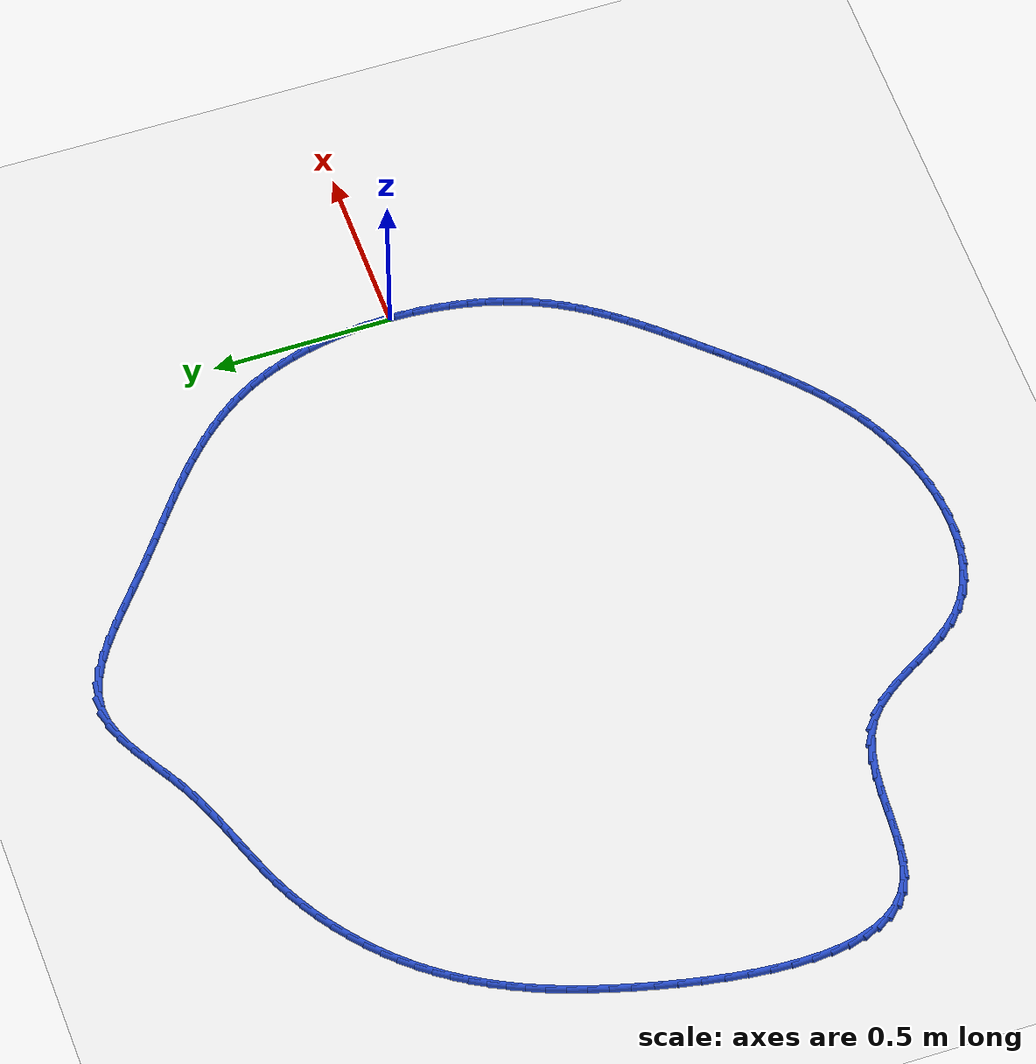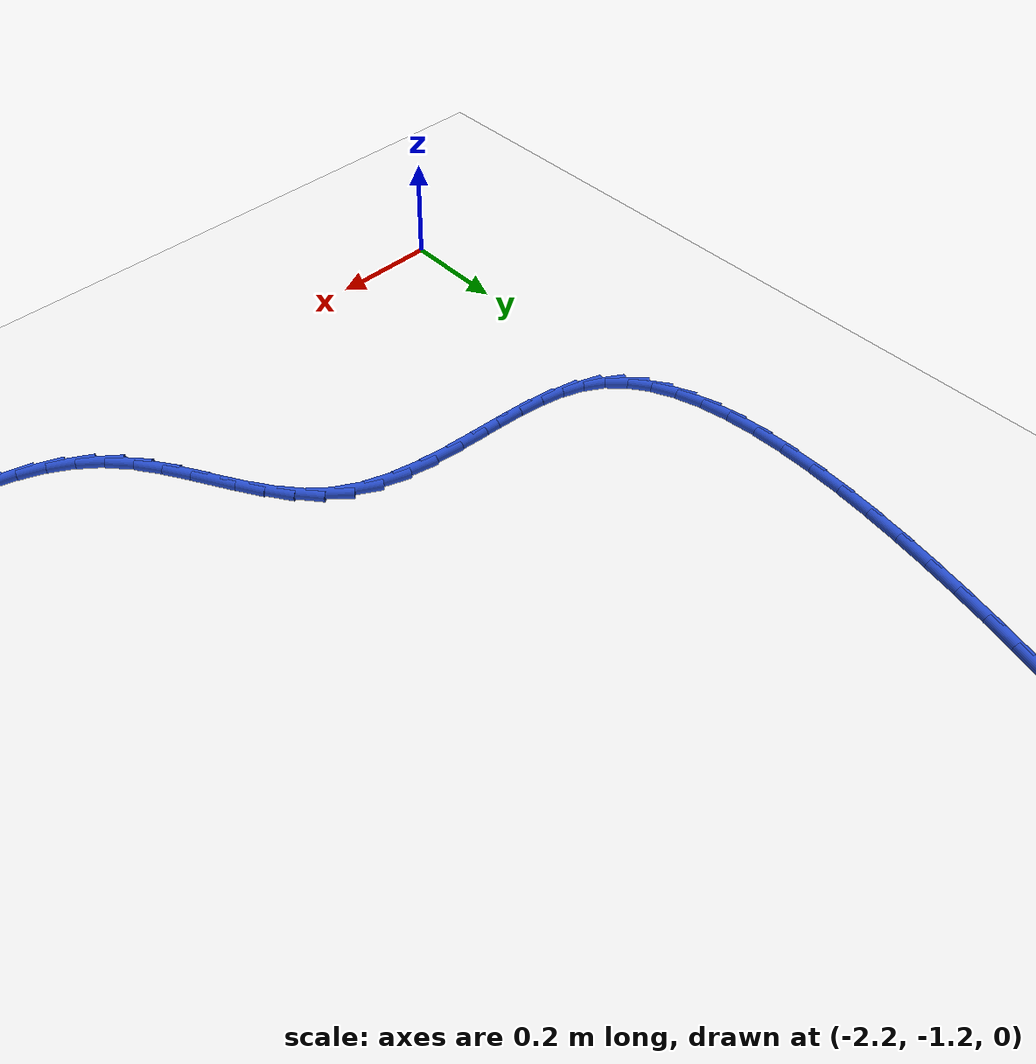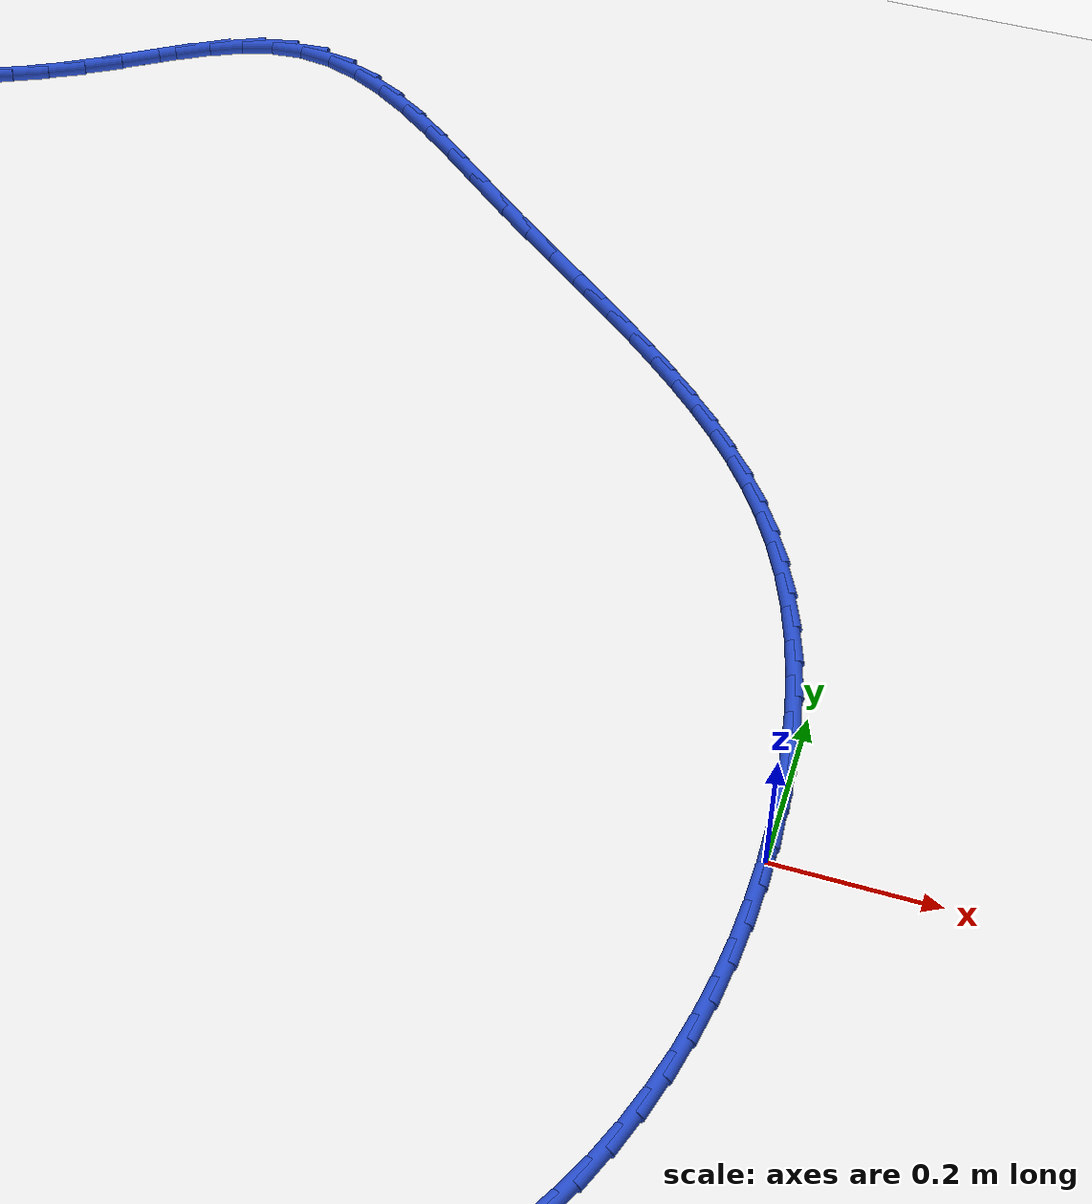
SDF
<sdf version="1.6">
 <world name="default">
  <light name="sun" type="directional">
   <pose>0 0 10 0 -0 0</pose>
   <diffuse>0.8 0.8 0.8 1</diffuse>
   <specular>0.2 0.2 0.2 1</specular>
   <attenuation>
    <range>1000</range>
    <constant>0.9</constant>
    <linear>0.01</linear>
    <quadratic>0.001</quadratic>
   </attenuation>
   <direction>-0.5 0.1 -0.9</direction>
  </light>
  <model name="ground_plane">
   <static>1</static>
   <link name="link">
    <collision name="collision">
     <geometry><plane><normal>0 0 1</normal><size>100 100</size></plane></geometry>
     <surface><friction><ode><mu>100</mu><mu2>50</mu2></ode></friction></surface>
    </collision>
    <visual name="visual">
     <cast_shadows>0</cast_shadows>
     <geometry><plane><normal>0 0 1</normal><size>100 100</size></plane></geometry>
     <material>
      <script><uri>file://media/materials/scripts/gazebo.material</uri><name>Gazebo/WhiteGlow</name></script>
     </material>
    </visual>
   </link>
  </model>
  <gravity>0 0 -9.8</gravity>
  <magnetic_field>6e-06 2.3e-05 -4.2e-05</magnetic_field>
  <atmosphere type="adiabatic"/>
  <physics name="default_physics" default="0" type="ode">
   <max_step_size>0.001</max_step_size>
   <real_time_factor>1</real_time_factor>
   <real_time_update_rate>1000</real_time_update_rate>
  </physics>
  <scene><ambient>0.4 0.4 0.4 1</ambient><background>0.7 0.7 0.7 1</background><shadows>1</shadows></scene>
  <spherical_coordinates>
   <surface_model>EARTH_WGS84</surface_model>
   <latitude_deg>0</latitude_deg>
   <longitude_deg>0</longitude_deg>
   <elevation>0</elevation>
   <heading_deg>0</heading_deg>
  </spherical_coordinates>
  <model name="line">
   <link name="link_0">
    <pose>2.949029909160572e-17 -4.163336342344337e-17 0.01 0 1.57 -1.5482628776437326</pose>
    <collision name="collision">
     <geometry><cylinder><radius>0.01</radius><length>0.08</length></cylinder></geometry>
    </collision>
    <visual name="visual">
     <material>
      <script><name>Gazebo/Blue</name><uri>file://media/materials/scripts/gazebo.material</uri></script>
     </material>
     <geometry><cylinder><radius>0.01</radius><length>0.08</length></cylinder></geometry>
    </visual>
   </link>
   <link name="link_1">
    <pose>-0.0011610782208647354 0.05151815381150185 0.01 0 1.57 -1.5023433477779056</pose>
    <collision name="collision">
     <geometry><cylinder><radius>0.01</radius><length>0.08</length></cylinder></geometry>
    </collision>
    <visual name="visual">
     <material>
      <script><name>Gazebo/Blue</name><uri>file://media/materials/scripts/gazebo.material</uri></script>
     </material>
     <geometry><cylinder><radius>0.01</radius><length>0.08</length></cylinder></geometry>
    </visual>
   </link>
   <link name="link_2">
    <pose>-0.004686851859591169 0.10294418278295633 0.01 0 1.57 -1.4547697596404423</pose>
    <collision name="collision">
     <geometry><cylinder><radius>0.01</radius><length>0.08</length></cylinder></geometry>
    </collision>
    <visual name="visual">
     <material>
      <script><name>Gazebo/Blue</name><uri>file://media/materials/scripts/gazebo.material</uri></script>
     </material>
     <geometry><cylinder><radius>0.01</radius><length>0.08</length></cylinder></geometry>
    </visual>
   </link>
   <link name="link_3">
    <pose>-0.010637041667062553 0.1539968438044139 0.01 0 1.57 -1.4049787457923235</pose>
    <collision name="collision">
     <geometry><cylinder><radius>0.01</radius><length>0.08</length></cylinder></geometry>
    </collision>
    <visual name="visual">
     <material>
      <script><name>Gazebo/Blue</name><uri>file://media/materials/scripts/gazebo.material</uri></script>
     </material>
     <geometry><cylinder><radius>0.01</radius><length>0.08</length></cylinder></geometry>
    </visual>
   </link>
   <link name="link_4">
    <pose>-0.019071368394162173 0.20439489376592485 0.01 0 1.57 -1.3523858434189278</pose>
    <collision name="collision">
     <geometry><cylinder><radius>0.01</radius><length>0.08</length></cylinder></geometry>
    </collision>
    <visual name="visual">
     <material>
      <script><name>Gazebo/Blue</name><uri>file://media/materials/scripts/gazebo.material</uri></script>
     </material>
     <geometry><cylinder><radius>0.01</radius><length>0.08</length></cylinder></geometry>
    </visual>
   </link>
   <link name="link_5">
    <pose>-0.030049552791773296 0.2538570895575396 0.01 0 1.57 -1.2963824746404804</pose>
    <collision name="collision">
     <geometry><cylinder><radius>0.01</radius><length>0.08</length></cylinder></geometry>
    </collision>
    <visual name="visual">
     <material>
      <script><name>Gazebo/Blue</name><uri>file://media/materials/scripts/gazebo.material</uri></script>
     </material>
     <geometry><cylinder><radius>0.01</radius><length>0.08</length></cylinder></geometry>
    </visual>
   </link>
   <link name="link_6">
    <pose>-0.04363131561077922 0.3021021880693086 0.01 0 1.57 -1.2363396563524172</pose>
    <collision name="collision">
     <geometry><cylinder><radius>0.01</radius><length>0.08</length></cylinder></geometry>
    </collision>
    <visual name="visual">
     <material>
      <script><name>Gazebo/Blue</name><uri>file://media/materials/scripts/gazebo.material</uri></script>
     </material>
     <geometry><cylinder><radius>0.01</radius><length>0.08</length></cylinder></geometry>
    </visual>
   </link>
   <link name="link_7">
    <pose>-0.05987637760206321 0.3488489461912823 0.01 0 1.57 -1.1716217137240348</pose>
    <collision name="collision">
     <geometry><cylinder><radius>0.01</radius><length>0.08</length></cylinder></geometry>
    </collision>
    <visual name="visual">
     <material>
      <script><name>Gazebo/Blue</name><uri>file://media/materials/scripts/gazebo.material</uri></script>
     </material>
     <geometry><cylinder><radius>0.01</radius><length>0.08</length></cylinder></geometry>
    </visual>
   </link>
   <link name="link_8">
    <pose>-0.07884445951650856 0.39381612081351103 0.01 0 1.57 -1.1016149077701611</pose>
    <collision name="collision">
     <geometry><cylinder><radius>0.01</radius><length>0.08</length></cylinder></geometry>
    </collision>
    <visual name="visual">
     <material>
      <script><name>Gazebo/Blue</name><uri>file://media/materials/scripts/gazebo.material</uri></script>
     </material>
     <geometry><cylinder><radius>0.01</radius><length>0.08</length></cylinder></geometry>
    </visual>
   </link>
   <link name="link_9">
    <pose>-0.10059526870024321 0.43672249679207065 0.01 0 1.57 -1.0279057046944653</pose>
    <collision name="collision">
     <geometry><cylinder><radius>0.01</radius><length>0.08</length></cylinder></geometry>
    </collision>
    <visual name="visual">
     <material>
      <script><name>Gazebo/Blue</name><uri>file://media/materials/scripts/gazebo.material</uri></script>
     </material>
     <geometry><cylinder><radius>0.01</radius><length>0.08</length></cylinder></geometry>
    </visual>
   </link>
   <link name="link_10">
    <pose>-0.12513622866354515 0.4773959375191431 0.01 0 1.57 -0.9578073523704165</pose>
    <collision name="collision">
     <geometry><cylinder><radius>0.01</radius><length>0.08</length></cylinder></geometry>
    </collision>
    <visual name="visual">
     <material>
      <script><name>Gazebo/Blue</name><uri>file://media/materials/scripts/gazebo.material</uri></script>
     </material>
     <geometry><cylinder><radius>0.01</radius><length>0.08</length></cylinder></geometry>
    </visual>
   </link>
   <link name="link_11">
    <pose>-0.15230396457458753 0.516020638947885 0.01 0 1.57 -0.8939057636603568</pose>
    <collision name="collision">
     <geometry><cylinder><radius>0.01</radius><length>0.08</length></cylinder></geometry>
    </collision>
    <visual name="visual">
     <material>
      <script><name>Gazebo/Blue</name><uri>file://media/materials/scripts/gazebo.material</uri></script>
     </material>
     <geometry><cylinder><radius>0.01</radius><length>0.08</length></cylinder></geometry>
    </visual>
   </link>
   <link name="link_12">
    <pose>-0.1819002809311496 0.5528534425765077 0.01 0 1.57 -0.8370627536945683</pose>
    <collision name="collision">
     <geometry><cylinder><radius>0.01</radius><length>0.08</length></cylinder></geometry>
    </collision>
    <visual name="visual">
     <material>
      <script><name>Gazebo/Blue</name><uri>file://media/materials/scripts/gazebo.material</uri></script>
     </material>
     <geometry><cylinder><radius>0.01</radius><length>0.08</length></cylinder></geometry>
    </visual>
   </link>
   <link name="link_13">
    <pose>-0.21372698223101025 0.5881511899032216 0.01 0 1.57 -0.7877647693739106</pose>
    <collision name="collision">
     <geometry><cylinder><radius>0.01</radius><length>0.08</length></cylinder></geometry>
    </collision>
    <visual name="visual">
     <material>
      <script><name>Gazebo/Blue</name><uri>file://media/materials/scripts/gazebo.material</uri></script>
     </material>
     <geometry><cylinder><radius>0.01</radius><length>0.08</length></cylinder></geometry>
    </visual>
   </link>
   <link name="link_14">
    <pose>-0.24758587297194853 0.622170722426238 0.01 0 1.57 -0.7461886213446509</pose>
    <collision name="collision">
     <geometry><cylinder><radius>0.01</radius><length>0.08</length></cylinder></geometry>
    </collision>
    <visual name="visual">
     <material>
      <script><name>Gazebo/Blue</name><uri>file://media/materials/scripts/gazebo.material</uri></script>
     </material>
     <geometry><cylinder><radius>0.01</radius><length>0.08</length></cylinder></geometry>
    </visual>
   </link>
   <link name="link_15">
    <pose>-0.28327875765174343 0.6551688816437676 0.01 0 1.57 -0.712284236588454</pose>
    <collision name="collision">
     <geometry><cylinder><radius>0.01</radius><length>0.08</length></cylinder></geometry>
    </collision>
    <visual name="visual">
     <material>
      <script><name>Gazebo/Blue</name><uri>file://media/materials/scripts/gazebo.material</uri></script>
     </material>
     <geometry><cylinder><radius>0.01</radius><length>0.08</length></cylinder></geometry>
    </visual>
   </link>
   <link name="link_16">
    <pose>-0.3206074407681741 0.6874025090540213 0.01 0 1.57 -0.6858541433763657</pose>
    <collision name="collision">
     <geometry><cylinder><radius>0.01</radius><length>0.08</length></cylinder></geometry>
    </collision>
    <visual name="visual">
     <material>
      <script><name>Gazebo/Blue</name><uri>file://media/materials/scripts/gazebo.material</uri></script>
     </material>
     <geometry><cylinder><radius>0.01</radius><length>0.08</length></cylinder></geometry>
    </visual>
   </link>
   <link name="link_17">
    <pose>-0.3593737268190195 0.7191284461552101 0.01 0 1.57 -0.6666186955933922</pose>
    <collision name="collision">
     <geometry><cylinder><radius>0.01</radius><length>0.08</length></cylinder></geometry>
    </collision>
    <visual name="visual">
     <material>
      <script><name>Gazebo/Blue</name><uri>file://media/materials/scripts/gazebo.material</uri></script>
     </material>
     <geometry><cylinder><radius>0.01</radius><length>0.08</length></cylinder></geometry>
    </visual>
   </link>
   <link name="link_18">
    <pose>-0.39937942030205853 0.7506035344455447 0.01 0 1.57 -0.6542635527888481</pose>
    <collision name="collision">
     <geometry><cylinder><radius>0.01</radius><length>0.08</length></cylinder></geometry>
    </collision>
    <visual name="visual">
     <material>
      <script><name>Gazebo/Blue</name><uri>file://media/materials/scripts/gazebo.material</uri></script>
     </material>
     <geometry><cylinder><radius>0.01</radius><length>0.08</length></cylinder></geometry>
    </visual>
   </link>
   <link name="link_19">
    <pose>-0.44042632571507057 0.7820846154232363 0.01 0 1.57 -0.6484703894406812</pose>
    <collision name="collision">
     <geometry><cylinder><radius>0.01</radius><length>0.08</length></cylinder></geometry>
    </collision>
    <visual name="visual">
     <material>
      <script><name>Gazebo/Blue</name><uri>file://media/materials/scripts/gazebo.material</uri></script>
     </material>
     <geometry><cylinder><radius>0.01</radius><length>0.08</length></cylinder></geometry>
    </visual>
   </link>
   <link name="link_20">
    <pose>-0.48231624755583435 0.8138285305864952 0.01 0 1.57 -0.6489337024176066</pose>
    <collision name="collision">
     <geometry><cylinder><radius>0.01</radius><length>0.08</length></cylinder></geometry>
    </collision>
    <visual name="visual">
     <material>
      <script><name>Gazebo/Blue</name><uri>file://media/materials/scripts/gazebo.material</uri></script>
     </material>
     <geometry><cylinder><radius>0.01</radius><length>0.08</length></cylinder></geometry>
    </visual>
   </link>
   <link name="link_21">
    <pose>-0.524850990322129 0.8460921214335329 0.01 0 1.57 -0.6553669138830422</pose>
    <collision name="collision">
     <geometry><cylinder><radius>0.01</radius><length>0.08</length></cylinder></geometry>
    </collision>
    <visual name="visual">
     <material>
      <script><name>Gazebo/Blue</name><uri>file://media/materials/scripts/gazebo.material</uri></script>
     </material>
     <geometry><cylinder><radius>0.01</radius><length>0.08</length></cylinder></geometry>
    </visual>
   </link>
   <link name="link_22">
    <pose>-0.5678323585117335 0.8791322294625599 0.01 0 1.57 -0.6674981503546676</pose>
    <collision name="collision">
     <geometry><cylinder><radius>0.01</radius><length>0.08</length></cylinder></geometry>
    </collision>
    <visual name="visual">
     <material>
      <script><name>Gazebo/Blue</name><uri>file://media/materials/scripts/gazebo.material</uri></script>
     </material>
     <geometry><cylinder><radius>0.01</radius><length>0.08</length></cylinder></geometry>
    </visual>
   </link>
   <link name="link_23">
    <pose>-0.6110621774168113 0.9132055423475768 0.01 0 1.57 -0.6798293805609592</pose>
    <collision name="collision">
     <geometry><cylinder><radius>0.01</radius><length>0.08</length></cylinder></geometry>
    </collision>
    <visual name="visual">
     <material>
      <script><name>Gazebo/Blue</name><uri>file://media/materials/scripts/gazebo.material</uri></script>
     </material>
     <geometry><cylinder><radius>0.01</radius><length>0.08</length></cylinder></geometry>
    </visual>
   </link>
   <link name="link_24">
    <pose>-0.6543881517482133 0.9482293597228247 0.01 0 1.57 -0.6761659838757637</pose>
    <collision name="collision">
     <geometry><cylinder><radius>0.01</radius><length>0.08</length></cylinder></geometry>
    </collision>
    <visual name="visual">
     <material>
      <script><name>Gazebo/Blue</name><uri>file://media/materials/scripts/gazebo.material</uri></script>
     </material>
     <geometry><cylinder><radius>0.01</radius><length>0.08</length></cylinder></geometry>
    </visual>
   </link>
   <link name="link_25">
    <pose>-0.6978012243047748 0.9830613929520214 0.01 0 1.57 -0.653028193894963</pose>
    <collision name="collision">
     <geometry><cylinder><radius>0.01</radius><length>0.08</length></cylinder></geometry>
    </collision>
    <visual name="visual">
     <material>
      <script><name>Gazebo/Blue</name><uri>file://media/materials/scripts/gazebo.material</uri></script>
     </material>
     <geometry><cylinder><radius>0.01</radius><length>0.08</length></cylinder></geometry>
    </visual>
   </link>
   <link name="link_26">
    <pose>-0.7413202138481925 1.0163531439772564 0.01 0 1.57 -0.6084520351411209</pose>
    <collision name="collision">
     <geometry><cylinder><radius>0.01</radius><length>0.08</length></cylinder></geometry>
    </collision>
    <visual name="visual">
     <material>
      <script><name>Gazebo/Blue</name><uri>file://media/materials/scripts/gazebo.material</uri></script>
     </material>
     <geometry><cylinder><radius>0.01</radius><length>0.08</length></cylinder></geometry>
    </visual>
   </link>
   <link name="link_27">
    <pose>-0.7849639391401632 1.0467561147406208 0.01 0 1.57 -0.5386262367026894</pose>
    <collision name="collision">
     <geometry><cylinder><radius>0.01</radius><length>0.08</length></cylinder></geometry>
    </collision>
    <visual name="visual">
     <material>
      <script><name>Gazebo/Blue</name><uri>file://media/materials/scripts/gazebo.material</uri></script>
     </material>
     <geometry><cylinder><radius>0.01</radius><length>0.08</length></cylinder></geometry>
    </visual>
   </link>
   <link name="link_28">
    <pose>-0.8287512189423847 1.0729218071842057 0.01 0 1.57 -0.43793571622098676</pose>
    <collision name="collision">
     <geometry><cylinder><radius>0.01</radius><length>0.08</length></cylinder></geometry>
    </collision>
    <visual name="visual">
     <material>
      <script><name>Gazebo/Blue</name><uri>file://media/materials/scripts/gazebo.material</uri></script>
     </material>
     <geometry><cylinder><radius>0.01</radius><length>0.08</length></cylinder></geometry>
    </visual>
   </link>
   <link name="link_29">
    <pose>-0.8727008720165531 1.0935017232501 0.01 0 1.57 -0.2998835933405029</pose>
    <collision name="collision">
     <geometry><cylinder><radius>0.01</radius><length>0.08</length></cylinder></geometry>
    </collision>
    <visual name="visual">
     <material>
      <script><name>Gazebo/Blue</name><uri>file://media/materials/scripts/gazebo.material</uri></script>
     </material>
     <geometry><cylinder><radius>0.01</radius><length>0.08</length></cylinder></geometry>
    </visual>
   </link>
   <link name="link_30">
    <pose>-0.9168317171243663 1.1071473648803958 0.01 0 1.57 -0.12038872570352807</pose>
    <collision name="collision">
     <geometry><cylinder><radius>0.01</radius><length>0.08</length></cylinder></geometry>
    </collision>
    <visual name="visual">
     <material>
      <script><name>Gazebo/Blue</name><uri>file://media/materials/scripts/gazebo.material</uri></script>
     </material>
     <geometry><cylinder><radius>0.01</radius><length>0.08</length></cylinder></geometry>
    </visual>
   </link>
   <link name="link_31">
    <pose>-0.9611625730275206 1.1125102340171826 0.01 0 1.57 0.09273850460463884</pose>
    <collision name="collision">
     <geometry><cylinder><radius>0.01</radius><length>0.08</length></cylinder></geometry>
    </collision>
    <visual name="visual">
     <material>
      <script><name>Gazebo/Blue</name><uri>file://media/materials/scripts/gazebo.material</uri></script>
     </material>
     <geometry><cylinder><radius>0.01</radius><length>0.08</length></cylinder></geometry>
    </visual>
   </link>
   <link name="link_32">
    <pose>-1.0057121970503786 1.1083668834894598 0.01 0 1.57 0.28189544279777</pose>
    <collision name="collision">
     <geometry><cylinder><radius>0.01</radius><length>0.08</length></cylinder></geometry>
    </collision>
    <visual name="visual">
     <material>
      <script><name>Gazebo/Blue</name><uri>file://media/materials/scripts/gazebo.material</uri></script>
     </material>
     <geometry><cylinder><radius>0.01</radius><length>0.08</length></cylinder></geometry>
    </visual>
   </link>
   <link name="link_33">
    <pose>-1.0504984117781844 1.095396454453954 0.01 0 1.57 0.4111525332569541</pose>
    <collision name="collision">
     <geometry><cylinder><radius>0.01</radius><length>0.08</length></cylinder></geometry>
    </collision>
    <visual name="visual">
     <material>
      <script><name>Gazebo/Blue</name><uri>file://media/materials/scripts/gazebo.material</uri></script>
     </material>
     <geometry><cylinder><radius>0.01</radius><length>0.08</length></cylinder></geometry>
    </visual>
   </link>
   <link name="link_34">
    <pose>-1.0955383122451297 1.0757589612995089 0.01 0 1.57 0.48892258509568687</pose>
    <collision name="collision">
     <geometry><cylinder><radius>0.01</radius><length>0.08</length></cylinder></geometry>
    </collision>
    <visual name="visual">
     <material>
      <script><name>Gazebo/Blue</name><uri>file://media/materials/scripts/gazebo.material</uri></script>
     </material>
     <geometry><cylinder><radius>0.01</radius><length>0.08</length></cylinder></geometry>
    </visual>
   </link>
   <link name="link_35">
    <pose>-1.1408489743030474 1.0516534626045682 0.01 0 1.57 0.5243902109966839</pose>
    <collision name="collision">
     <geometry><cylinder><radius>0.01</radius><length>0.08</length></cylinder></geometry>
    </collision>
    <visual name="visual">
     <material>
      <script><name>Gazebo/Blue</name><uri>file://media/materials/scripts/gazebo.material</uri></script>
     </material>
     <geometry><cylinder><radius>0.01</radius><length>0.08</length></cylinder></geometry>
    </visual>
   </link>
   <link name="link_36">
    <pose>-1.1864474738037711 1.025279016947574 0.01 0 1.57 0.5226503911864777</pose>
    <collision name="collision">
     <geometry><cylinder><radius>0.01</radius><length>0.08</length></cylinder></geometry>
    </collision>
    <visual name="visual">
     <material>
      <script><name>Gazebo/Blue</name><uri>file://media/materials/scripts/gazebo.material</uri></script>
     </material>
     <geometry><cylinder><radius>0.01</radius><length>0.08</length></cylinder></geometry>
    </visual>
   </link>
   <link name="link_37">
    <pose>-1.2323508865991348 0.9988346829069699 0.01 0 1.57 0.4849000655583541</pose>
    <collision name="collision">
     <geometry><cylinder><radius>0.01</radius><length>0.08</length></cylinder></geometry>
    </collision>
    <visual name="visual">
     <material>
      <script><name>Gazebo/Blue</name><uri>file://media/materials/scripts/gazebo.material</uri></script>
     </material>
     <geometry><cylinder><radius>0.01</radius><length>0.08</length></cylinder></geometry>
    </visual>
   </link>
   <link name="link_38">
    <pose>-1.2785745339003312 0.9744815240795265 0.01 0 1.57 0.43073374836021844</pose>
    <collision name="collision">
     <geometry><cylinder><radius>0.01</radius><length>0.08</length></cylinder></geometry>
    </collision>
    <visual name="visual">
     <material>
      <script><name>Gazebo/Blue</name><uri>file://media/materials/scripts/gazebo.material</uri></script>
     </material>
     <geometry><cylinder><radius>0.01</radius><length>0.08</length></cylinder></geometry>
    </visual>
   </link>
   <link name="link_39">
    <pose>-1.3250752445395635 0.9531140103119103 0.01 0 1.57 0.3870451447340628</pose>
    <collision name="collision">
     <geometry><cylinder><radius>0.01</radius><length>0.08</length></cylinder></geometry>
    </collision>
    <visual name="visual">
     <material>
      <script><name>Gazebo/Blue</name><uri>file://media/materials/scripts/gazebo.material</uri></script>
     </material>
     <geometry><cylinder><radius>0.01</radius><length>0.08</length></cylinder></geometry>
    </visual>
   </link>
   <link name="link_40">
    <pose>-1.3717390520567645 0.934093610463802 0.01 0 1.57 0.35666571631247734</pose>
    <collision name="collision">
     <geometry><cylinder><radius>0.01</radius><length>0.08</length></cylinder></geometry>
    </collision>
    <visual name="visual">
     <material>
      <script><name>Gazebo/Blue</name><uri>file://media/materials/scripts/gazebo.material</uri></script>
     </material>
     <geometry><cylinder><radius>0.01</radius><length>0.08</length></cylinder></geometry>
    </visual>
   </link>
   <link name="link_41">
    <pose>-1.4184477466259169 0.9166899075648719 0.01 0 1.57 0.3403958233441304</pose>
    <collision name="collision">
     <geometry><cylinder><radius>0.01</radius><length>0.08</length></cylinder></geometry>
    </collision>
    <visual name="visual">
     <material>
      <script><name>Gazebo/Blue</name><uri>file://media/materials/scripts/gazebo.material</uri></script>
     </material>
     <geometry><cylinder><radius>0.01</radius><length>0.08</length></cylinder></geometry>
    </visual>
   </link>
   <link name="link_42">
    <pose>-1.465083118421002 0.9001724846447896 0.01 0 1.57 0.33871076461163846</pose>
    <collision name="collision">
     <geometry><cylinder><radius>0.01</radius><length>0.08</length></cylinder></geometry>
    </collision>
    <visual name="visual">
     <material>
      <script><name>Gazebo/Blue</name><uri>file://media/materials/scripts/gazebo.material</uri></script>
     </material>
     <geometry><cylinder><radius>0.01</radius><length>0.08</length></cylinder></geometry>
    </visual>
   </link>
   <link name="link_43">
    <pose>-1.5115269576160026 0.8838109247332249 0.01 0 1.57 0.35183220017087274</pose>
    <collision name="collision">
     <geometry><cylinder><radius>0.01</radius><length>0.08</length></cylinder></geometry>
    </collision>
    <visual name="visual">
     <material>
      <script><name>Gazebo/Blue</name><uri>file://media/materials/scripts/gazebo.material</uri></script>
     </material>
     <geometry><cylinder><radius>0.01</radius><length>0.08</length></cylinder></geometry>
    </visual>
   </link>
   <link name="link_44">
    <pose>-1.5576610543849017 0.8668748108598482 0.01 0 1.57 0.37972579258217887</pose>
    <collision name="collision">
     <geometry><cylinder><radius>0.01</radius><length>0.08</length></cylinder></geometry>
    </collision>
    <visual name="visual">
     <material>
      <script><name>Gazebo/Blue</name><uri>file://media/materials/scripts/gazebo.material</uri></script>
     </material>
     <geometry><cylinder><radius>0.01</radius><length>0.08</length></cylinder></geometry>
    </visual>
   </link>
   <link name="link_45">
    <pose>-1.6033671989016798 0.8486337260543294 0.01 0 1.57 0.4220101628515285</pose>
    <collision name="collision">
     <geometry><cylinder><radius>0.01</radius><length>0.08</length></cylinder></geometry>
    </collision>
    <visual name="visual">
     <material>
      <script><name>Gazebo/Blue</name><uri>file://media/materials/scripts/gazebo.material</uri></script>
     </material>
     <geometry><cylinder><radius>0.01</radius><length>0.08</length></cylinder></geometry>
    </visual>
   </link>
   <link name="link_46">
    <pose>-1.6485271398611026 0.8283575556630598 0.01 0 1.57 0.4741432422492783</pose>
    <collision name="collision">
     <geometry><cylinder><radius>0.01</radius><length>0.08</length></cylinder></geometry>
    </collision>
    <visual name="visual">
     <material>
      <script><name>Gazebo/Blue</name><uri>file://media/materials/scripts/gazebo.material</uri></script>
     </material>
     <geometry><cylinder><radius>0.01</radius><length>0.08</length></cylinder></geometry>
    </visual>
   </link>
   <link name="link_47">
    <pose>-1.6929921079084036 0.8055386124783781 0.01 0 1.57 0.525624349857981</pose>
    <collision name="collision">
     <geometry><cylinder><radius>0.01</radius><length>0.08</length></cylinder></geometry>
    </collision>
    <visual name="visual">
     <material>
      <script><name>Gazebo/Blue</name><uri>file://media/materials/scripts/gazebo.material</uri></script>
     </material>
     <geometry><cylinder><radius>0.01</radius><length>0.08</length></cylinder></geometry>
    </visual>
   </link>
   <link name="link_48">
    <pose>-1.7365288525371525 0.7802849408706761 0.01 0 1.57 0.5753820322733207</pose>
    <collision name="collision">
     <geometry><cylinder><radius>0.01</radius><length>0.08</length></cylinder></geometry>
    </collision>
    <visual name="visual">
     <material>
      <script><name>Gazebo/Blue</name><uri>file://media/materials/scripts/gazebo.material</uri></script>
     </material>
     <geometry><cylinder><radius>0.01</radius><length>0.08</length></cylinder></geometry>
    </visual>
   </link>
   <link name="link_49">
    <pose>-1.778889625922694 0.752810247319039 0.01 0 1.57 0.6241409652063513</pose>
    <collision name="collision">
     <geometry><cylinder><radius>0.01</radius><length>0.08</length></cylinder></geometry>
    </collision>
    <visual name="visual">
     <material>
      <script><name>Gazebo/Blue</name><uri>file://media/materials/scripts/gazebo.material</uri></script>
     </material>
     <geometry><cylinder><radius>0.01</radius><length>0.08</length></cylinder></geometry>
    </visual>
   </link>
   <link name="link_50">
    <pose>-1.8198266802403709 0.7233282383025506 0.01 0 1.57 0.6726121496878623</pose>
    <collision name="collision">
     <geometry><cylinder><radius>0.01</radius><length>0.08</length></cylinder></geometry>
    </collision>
    <visual name="visual">
     <material>
      <script><name>Gazebo/Blue</name><uri>file://media/materials/scripts/gazebo.material</uri></script>
     </material>
     <geometry><cylinder><radius>0.01</radius><length>0.08</length></cylinder></geometry>
    </visual>
   </link>
   <link name="link_51">
    <pose>-1.8590922676655257 0.6920526203002954 0.01 0 1.57 0.7215146821076641</pose>
    <collision name="collision">
     <geometry><cylinder><radius>0.01</radius><length>0.08</length></cylinder></geometry>
    </collision>
    <visual name="visual">
     <material>
      <script><name>Gazebo/Blue</name><uri>file://media/materials/scripts/gazebo.material</uri></script>
     </material>
     <geometry><cylinder><radius>0.01</radius><length>0.08</length></cylinder></geometry>
    </visual>
   </link>
   <link name="link_52">
    <pose>-1.8964386403735027 0.6591970997913577 0.01 0 1.57 0.7715987007077882</pose>
    <collision name="collision">
     <geometry><cylinder><radius>0.01</radius><length>0.08</length></cylinder></geometry>
    </collision>
    <visual name="visual">
     <material>
      <script><name>Gazebo/Blue</name><uri>file://media/materials/scripts/gazebo.material</uri></script>
     </material>
     <geometry><cylinder><radius>0.01</radius><length>0.08</length></cylinder></geometry>
    </visual>
   </link>
   <link name="link_53">
    <pose>-1.9316183514721983 0.6249751550480994 0.01 0 1.57 0.8232298959714698</pose>
    <collision name="collision">
     <geometry><cylinder><radius>0.01</radius><length>0.08</length></cylinder></geometry>
    </collision>
    <visual name="visual">
     <material>
      <script><name>Gazebo/Blue</name><uri>file://media/materials/scripts/gazebo.material</uri></script>
     </material>
     <geometry><cylinder><radius>0.01</radius><length>0.08</length></cylinder></geometry>
    </visual>
   </link>
   <link name="link_54">
    <pose>-1.9644818859466915 0.5895259994869505 0.01 0 1.57 0.8754490096621762</pose>
    <collision name="collision">
     <geometry><cylinder><radius>0.01</radius><length>0.08</length></cylinder></geometry>
    </collision>
    <visual name="visual">
     <material>
      <script><name>Gazebo/Blue</name><uri>file://media/materials/scripts/gazebo.material</uri></script>
     </material>
     <geometry><cylinder><radius>0.01</radius><length>0.08</length></cylinder></geometry>
    </visual>
   </link>
   <link name="link_55">
    <pose>-1.9951179968079762 0.5528081603052413 0.01 0 1.57 0.9274336104759239</pose>
    <collision name="collision">
     <geometry><cylinder><radius>0.01</radius><length>0.08</length></cylinder></geometry>
    </collision>
    <visual name="visual">
     <material>
      <script><name>Gazebo/Blue</name><uri>file://media/materials/scripts/gazebo.material</uri></script>
     </material>
     <geometry><cylinder><radius>0.01</radius><length>0.08</length></cylinder></geometry>
    </visual>
   </link>
   <link name="link_56">
    <pose>-2.023650981002434 0.5147532106040802 0.01 0 1.57 0.9784699401962835</pose>
    <collision name="collision">
     <geometry><cylinder><radius>0.01</radius><length>0.08</length></cylinder></geometry>
    </collision>
    <visual name="visual">
     <material>
      <script><name>Gazebo/Blue</name><uri>file://media/materials/scripts/gazebo.material</uri></script>
     </material>
     <geometry><cylinder><radius>0.01</radius><length>0.08</length></cylinder></geometry>
    </visual>
   </link>
   <link name="link_57">
    <pose>-2.0502051354764452 0.4752927234845747 0.01 0 1.57 1.0278846288194967</pose>
    <collision name="collision">
     <geometry><cylinder><radius>0.01</radius><length>0.08</length></cylinder></geometry>
    </collision>
    <visual name="visual">
     <material>
      <script><name>Gazebo/Blue</name><uri>file://media/materials/scripts/gazebo.material</uri></script>
     </material>
     <geometry><cylinder><radius>0.01</radius><length>0.08</length></cylinder></geometry>
    </visual>
   </link>
   <link name="link_58">
    <pose>-2.074904757176392 0.43435827204783317 0.01 0 1.57 1.0750819653784671</pose>
    <collision name="collision">
     <geometry><cylinder><radius>0.01</radius><length>0.08</length></cylinder></geometry>
    </collision>
    <visual name="visual">
     <material>
      <script><name>Gazebo/Blue</name><uri>file://media/materials/scripts/gazebo.material</uri></script>
     </material>
     <geometry><cylinder><radius>0.01</radius><length>0.08</length></cylinder></geometry>
    </visual>
   </link>
   <link name="link_59">
    <pose>-2.0978741430486543 0.3918814293949631 0.01 0 1.57 1.119570774490355</pose>
    <collision name="collision">
     <geometry><cylinder><radius>0.01</radius><length>0.08</length></cylinder></geometry>
    </collision>
    <visual name="visual">
     <material>
      <script><name>Gazebo/Blue</name><uri>file://media/materials/scripts/gazebo.material</uri></script>
     </material>
     <geometry><cylinder><radius>0.01</radius><length>0.08</length></cylinder></geometry>
    </visual>
   </link>
   <link name="link_60">
    <pose>-2.119237590039615 0.3477937686270733 0.01 0 1.57 1.1609786585416302</pose>
    <collision name="collision">
     <geometry><cylinder><radius>0.01</radius><length>0.08</length></cylinder></geometry>
    </collision>
    <visual name="visual">
     <material>
      <script><name>Gazebo/Blue</name><uri>file://media/materials/scripts/gazebo.material</uri></script>
     </material>
     <geometry><cylinder><radius>0.01</radius><length>0.08</length></cylinder></geometry>
    </visual>
   </link>
   <link name="link_61">
    <pose>-2.139119395095654 0.30202686284527075 0.01 0 1.57 1.1990539784446084</pose>
    <collision name="collision">
     <geometry><cylinder><radius>0.01</radius><length>0.08</length></cylinder></geometry>
    </collision>
    <visual name="visual">
     <material>
      <script><name>Gazebo/Blue</name><uri>file://media/materials/scripts/gazebo.material</uri></script>
     </material>
     <geometry><cylinder><radius>0.01</radius><length>0.08</length></cylinder></geometry>
    </visual>
   </link>
   <link name="link_62">
    <pose>-2.157643855163153 0.2545122851506643 0.01 0 1.57 1.2336579102944303</pose>
    <collision name="collision">
     <geometry><cylinder><radius>0.01</radius><length>0.08</length></cylinder></geometry>
    </collision>
    <visual name="visual">
     <material>
      <script><name>Gazebo/Blue</name><uri>file://media/materials/scripts/gazebo.material</uri></script>
     </material>
     <geometry><cylinder><radius>0.01</radius><length>0.08</length></cylinder></geometry>
    </visual>
   </link>
   <link name="link_63">
    <pose>-2.174935267188493 0.2051816086443611 0.01 0 1.57 1.2647498727843163</pose>
    <collision name="collision">
     <geometry><cylinder><radius>0.01</radius><length>0.08</length></cylinder></geometry>
    </collision>
    <visual name="visual">
     <material>
      <script><name>Gazebo/Blue</name><uri>file://media/materials/scripts/gazebo.material</uri></script>
     </material>
     <geometry><cylinder><radius>0.01</radius><length>0.08</length></cylinder></geometry>
    </visual>
   </link>
   <link name="link_64">
    <pose>-2.191117928118057 0.15396640642747011 0.01 0 1.57 1.2923696405302105</pose>
    <collision name="collision">
     <geometry><cylinder><radius>0.01</radius><length>0.08</length></cylinder></geometry>
    </collision>
    <visual name="visual">
     <material>
      <script><name>Gazebo/Blue</name><uri>file://media/materials/scripts/gazebo.material</uri></script>
     </material>
     <geometry><cylinder><radius>0.01</radius><length>0.08</length></cylinder></geometry>
    </visual>
   </link>
   <link name="link_65">
    <pose>-2.206316134898223 0.1007982516010987 0.01 0 1.57 1.3166188629480584</pose>
    <collision name="collision">
     <geometry><cylinder><radius>0.01</radius><length>0.08</length></cylinder></geometry>
    </collision>
    <visual name="visual">
     <material>
      <script><name>Gazebo/Blue</name><uri>file://media/materials/scripts/gazebo.material</uri></script>
     </material>
     <geometry><cylinder><radius>0.01</radius><length>0.08</length></cylinder></geometry>
    </visual>
   </link>
   <link name="link_66">
    <pose>-2.220654184475375 0.04560871726635454 0.01 0 1.57 1.3382843014080097</pose>
    <collision name="collision">
     <geometry><cylinder><radius>0.01</radius><length>0.08</length></cylinder></geometry>
    </collision>
    <visual name="visual">
     <material>
      <script><name>Gazebo/Blue</name><uri>file://media/materials/scripts/gazebo.material</uri></script>
     </material>
     <geometry><cylinder><radius>0.01</radius><length>0.08</length></cylinder></geometry>
    </visual>
   </link>
   <link name="link_67">
    <pose>-2.2341989973262977 -0.011591948873490772 0.01 0 1.57 1.3613842115149624</pose>
    <collision name="collision">
     <geometry><cylinder><radius>0.01</radius><length>0.08</length></cylinder></geometry>
    </collision>
    <visual name="visual">
     <material>
      <script><name>Gazebo/Blue</name><uri>file://media/materials/scripts/gazebo.material</uri></script>
     </material>
     <geometry><cylinder><radius>0.01</radius><length>0.08</length></cylinder></geometry>
    </visual>
   </link>
   <link name="link_68">
    <pose>-2.246683709258955 -0.07033581365259546 0.01 0 1.57 1.3878424840213663</pose>
    <collision name="collision">
     <geometry><cylinder><radius>0.01</radius><length>0.08</length></cylinder></geometry>
    </collision>
    <visual name="visual">
     <material>
      <script><name>Gazebo/Blue</name><uri>file://media/materials/scripts/gazebo.material</uri></script>
     </material>
     <geometry><cylinder><radius>0.01</radius><length>0.08</length></cylinder></geometry>
    </visual>
   </link>
   <link name="link_69">
    <pose>-2.257721072433514 -0.1299898738744201 0.01 0 1.57 1.4184331368081344</pose>
    <collision name="collision">
     <geometry><cylinder><radius>0.01</radius><length>0.08</length></cylinder></geometry>
    </collision>
    <visual name="visual">
     <material>
      <script><name>Gazebo/Blue</name><uri>file://media/materials/scripts/gazebo.material</uri></script>
     </material>
     <geometry><cylinder><radius>0.01</radius><length>0.08</length></cylinder></geometry>
    </visual>
   </link>
   <link name="link_70">
    <pose>-2.2669236773338524 -0.18992090465193703 0.01 0 1.57 1.454157151650541</pose>
    <collision name="collision">
     <geometry><cylinder><radius>0.01</radius><length>0.08</length></cylinder></geometry>
    </collision>
    <visual name="visual">
     <material>
      <script><name>Gazebo/Blue</name><uri>file://media/materials/scripts/gazebo.material</uri></script>
     </material>
     <geometry><cylinder><radius>0.01</radius><length>0.08</length></cylinder></geometry>
    </visual>
   </link>
   <link name="link_71">
    <pose>-2.27390411444385 -0.24949568109811743 0.01 0 1.57 1.4963275208523752</pose>
    <collision name="collision">
     <geometry><cylinder><radius>0.01</radius><length>0.08</length></cylinder></geometry>
    </collision>
    <visual name="visual">
     <material>
      <script><name>Gazebo/Blue</name><uri>file://media/materials/scripts/gazebo.material</uri></script>
     </material>
     <geometry><cylinder><radius>0.01</radius><length>0.08</length></cylinder></geometry>
    </visual>
   </link>
   <link name="link_72">
    <pose>-2.2782749742473847 -0.3080809783259331 0.01 0 1.57 1.546682138945033</pose>
    <collision name="collision">
     <geometry><cylinder><radius>0.01</radius><length>0.08</length></cylinder></geometry>
    </collision>
    <visual name="visual">
     <material>
      <script><name>Gazebo/Blue</name><uri>file://media/materials/scripts/gazebo.material</uri></script>
     </material>
     <geometry><cylinder><radius>0.01</radius><length>0.08</length></cylinder></geometry>
    </visual>
   </link>
   <link name="link_73">
    <pose>-2.2796488472283354 -0.36504357144835664 0.01 0 1.57 -1.5340618820628</pose>
    <collision name="collision">
     <geometry><cylinder><radius>0.01</radius><length>0.08</length></cylinder></geometry>
    </collision>
    <visual name="visual">
     <material>
      <script><name>Gazebo/Blue</name><uri>file://media/materials/scripts/gazebo.material</uri></script>
     </material>
     <geometry><cylinder><radius>0.01</radius><length>0.08</length></cylinder></geometry>
    </visual>
   </link>
   <link name="link_74">
    <pose>-2.27763832387058 -0.4197502355783582 0.01 0 1.57 -1.4596658292979567</pose>
    <collision name="collision">
     <geometry><cylinder><radius>0.01</radius><length>0.08</length></cylinder></geometry>
    </collision>
    <visual name="visual">
     <material>
      <script><name>Gazebo/Blue</name><uri>file://media/materials/scripts/gazebo.material</uri></script>
     </material>
     <geometry><cylinder><radius>0.01</radius><length>0.08</length></cylinder></geometry>
    </visual>
   </link>
   <link name="link_75">
    <pose>-2.271855994657999 -0.47156774582891026 0.01 0 1.57 -1.3677823106162332</pose>
    <collision name="collision">
     <geometry><cylinder><radius>0.01</radius><length>0.08</length></cylinder></geometry>
    </collision>
    <visual name="visual">
     <material>
      <script><name>Gazebo/Blue</name><uri>file://media/materials/scripts/gazebo.material</uri></script>
     </material>
     <geometry><cylinder><radius>0.01</radius><length>0.08</length></cylinder></geometry>
    </visual>
   </link>
   <link name="link_76">
    <pose>-2.261914450074469 -0.5198628773129844 0.01 0 1.57 -1.2536406235856041</pose>
    <collision name="collision">
     <geometry><cylinder><radius>0.01</radius><length>0.08</length></cylinder></geometry>
    </collision>
    <visual name="visual">
     <material>
      <script><name>Gazebo/Blue</name><uri>file://media/materials/scripts/gazebo.material</uri></script>
     </material>
     <geometry><cylinder><radius>0.01</radius><length>0.08</length></cylinder></geometry>
    </visual>
   </link>
   <link name="link_77">
    <pose>-2.2474262806038694 -0.5640024051435524 0.01 0 1.57 -1.1123084045248075</pose>
    <collision name="collision">
     <geometry><cylinder><radius>0.01</radius><length>0.08</length></cylinder></geometry>
    </collision>
    <visual name="visual">
     <material>
      <script><name>Gazebo/Blue</name><uri>file://media/materials/scripts/gazebo.material</uri></script>
     </material>
     <geometry><cylinder><radius>0.01</radius><length>0.08</length></cylinder></geometry>
    </visual>
   </link>
   <link name="link_78">
    <pose>-2.2280040767300786 -0.6033531044335864 0.01 0 1.57 -0.9406852551084782</pose>
    <collision name="collision">
     <geometry><cylinder><radius>0.01</radius><length>0.08</length></cylinder></geometry>
    </collision>
    <visual name="visual">
     <material>
      <script><name>Gazebo/Blue</name><uri>file://media/materials/scripts/gazebo.material</uri></script>
     </material>
     <geometry><cylinder><radius>0.01</radius><length>0.08</length></cylinder></geometry>
    </visual>
   </link>
   <link name="link_79">
    <pose>-2.2032604289369764 -0.6372817502960573 0.01 0 1.57 -0.741207572414806</pose>
    <collision name="collision">
     <geometry><cylinder><radius>0.01</radius><length>0.08</length></cylinder></geometry>
    </collision>
    <visual name="visual">
     <material>
      <script><name>Gazebo/Blue</name><uri>file://media/materials/scripts/gazebo.material</uri></script>
     </material>
     <geometry><cylinder><radius>0.01</radius><length>0.08</length></cylinder></geometry>
    </visual>
   </link>
   <link name="link_80">
    <pose>-2.172807927708439 -0.6651551178439365 0.01 0 1.57 -0.5260594746920976</pose>
    <collision name="collision">
     <geometry><cylinder><radius>0.01</radius><length>0.08</length></cylinder></geometry>
    </collision>
    <visual name="visual">
     <material>
      <script><name>Gazebo/Blue</name><uri>file://media/materials/scripts/gazebo.material</uri></script>
     </material>
     <geometry><cylinder><radius>0.01</radius><length>0.08</length></cylinder></geometry>
    </visual>
   </link>
   <link name="link_81">
    <pose>-2.1362782043076045 -0.6863655857820175 0.01 0 1.57 -0.3373671586808228</pose>
    <collision name="collision">
     <geometry><cylinder><radius>0.01</radius><length>0.08</length></cylinder></geometry>
    </collision>
    <visual name="visual">
     <material>
      <script><name>Gazebo/Blue</name><uri>file://media/materials/scripts/gazebo.material</uri></script>
     </material>
     <geometry><cylinder><radius>0.01</radius><length>0.08</length></cylinder></geometry>
    </visual>
   </link>
   <link name="link_82">
    <pose>-2.0939722227432904 -0.7012055654335568 0.01 0 1.57 -0.2073817738236382</pose>
    <collision name="collision">
     <geometry><cylinder><radius>0.01</radius><length>0.08</length></cylinder></geometry>
    </collision>
    <visual name="visual">
     <material>
      <script><name>Gazebo/Blue</name><uri>file://media/materials/scripts/gazebo.material</uri></script>
     </material>
     <geometry><cylinder><radius>0.01</radius><length>0.08</length></cylinder></geometry>
    </visual>
   </link>
   <link name="link_83">
    <pose>-2.047021517667985 -0.711084312734696 0.01 0 1.57 -0.126207193546715</pose>
    <collision name="collision">
     <geometry><cylinder><radius>0.01</radius><length>0.08</length></cylinder></geometry>
    </collision>
    <visual name="visual">
     <material>
      <script><name>Gazebo/Blue</name><uri>file://media/materials/scripts/gazebo.material</uri></script>
     </material>
     <geometry><cylinder><radius>0.01</radius><length>0.08</length></cylinder></geometry>
    </visual>
   </link>
   <link name="link_84">
    <pose>-1.9966093837296304 -0.7174806838085401 0.01 0 1.57 -0.08317883889698062</pose>
    <collision name="collision">
     <geometry><cylinder><radius>0.01</radius><length>0.08</length></cylinder></geometry>
    </collision>
    <visual name="visual">
     <material>
      <script><name>Gazebo/Blue</name><uri>file://media/materials/scripts/gazebo.material</uri></script>
     </material>
     <geometry><cylinder><radius>0.01</radius><length>0.08</length></cylinder></geometry>
    </visual>
   </link>
   <link name="link_85">
    <pose>-1.9439191155761673 -0.7218735347781927 0.01 0 1.57 -0.07179567956582938</pose>
    <collision name="collision">
     <geometry><cylinder><radius>0.01</radius><length>0.08</length></cylinder></geometry>
    </collision>
    <visual name="visual">
     <material>
      <script><name>Gazebo/Blue</name><uri>file://media/materials/scripts/gazebo.material</uri></script>
     </material>
     <geometry><cylinder><radius>0.01</radius><length>0.08</length></cylinder></geometry>
    </visual>
   </link>
   <link name="link_86">
    <pose>-1.8901340078555378 -0.7257417217667583 0.01 0 1.57 -0.08956753166701856</pose>
    <collision name="collision">
     <geometry><cylinder><radius>0.01</radius><length>0.08</length></cylinder></geometry>
    </collision>
    <visual name="visual">
     <material>
      <script><name>Gazebo/Blue</name><uri>file://media/materials/scripts/gazebo.material</uri></script>
     </material>
     <geometry><cylinder><radius>0.01</radius><length>0.08</length></cylinder></geometry>
    </visual>
   </link>
   <link name="link_87">
    <pose>-1.8364373552156819 -0.7305641008973409 0.01 0 1.57 -0.1375230017352444</pose>
    <collision name="collision">
     <geometry><cylinder><radius>0.01</radius><length>0.08</length></cylinder></geometry>
    </collision>
    <visual name="visual">
     <material>
      <script><name>Gazebo/Blue</name><uri>file://media/materials/scripts/gazebo.material</uri></script>
     </material>
     <geometry><cylinder><radius>0.01</radius><length>0.08</length></cylinder></geometry>
    </visual>
   </link>
   <link name="link_88">
    <pose>-1.7840124523045437 -0.7378195282930449 0.01 0 1.57 -0.21986850662432864</pose>
    <collision name="collision">
     <geometry><cylinder><radius>0.01</radius><length>0.08</length></cylinder></geometry>
    </collision>
    <visual name="visual">
     <material>
      <script><name>Gazebo/Blue</name><uri>file://media/materials/scripts/gazebo.material</uri></script>
     </material>
     <geometry><cylinder><radius>0.01</radius><length>0.08</length></cylinder></geometry>
    </visual>
   </link>
   <link name="link_89">
    <pose>-1.7340425937700628 -0.7489868600769742 0.01 0 1.57 -0.343236803186289</pose>
    <collision name="collision">
     <geometry><cylinder><radius>0.01</radius><length>0.08</length></cylinder></geometry>
    </collision>
    <visual name="visual">
     <material>
      <script><name>Gazebo/Blue</name><uri>file://media/materials/scripts/gazebo.material</uri></script>
     </material>
     <geometry><cylinder><radius>0.01</radius><length>0.08</length></cylinder></geometry>
    </visual>
   </link>
   <link name="link_90">
    <pose>-1.6877110742601817 -0.7655449523722331 0.01 0 1.57 -0.5137502279021221</pose>
    <collision name="collision">
     <geometry><cylinder><radius>0.01</radius><length>0.08</length></cylinder></geometry>
    </collision>
    <visual name="visual">
     <material>
      <script><name>Gazebo/Blue</name><uri>file://media/materials/scripts/gazebo.material</uri></script>
     </material>
     <geometry><cylinder><radius>0.01</radius><length>0.08</length></cylinder></geometry>
    </visual>
   </link>
   <link name="link_91">
    <pose>-1.6461990546407372 -0.788969881850291 0.01 0 1.57 -0.7070441552987657</pose>
    <collision name="collision">
     <geometry><cylinder><radius>0.01</radius><length>0.08</length></cylinder></geometry>
    </collision>
    <visual name="visual">
     <material>
      <script><name>Gazebo/Blue</name><uri>file://media/materials/scripts/gazebo.material</uri></script>
     </material>
     <geometry><cylinder><radius>0.01</radius><length>0.08</length></cylinder></geometry>
    </visual>
   </link>
   <link name="link_92">
    <pose>-1.6100261904590203 -0.819876052364025 0.01 0 1.57 -0.8581318931787117</pose>
    <collision name="collision">
     <geometry><cylinder><radius>0.01</radius><length>0.08</length></cylinder></geometry>
    </collision>
    <visual name="visual">
     <material>
      <script><name>Gazebo/Blue</name><uri>file://media/materials/scripts/gazebo.material</uri></script>
     </material>
     <geometry><cylinder><radius>0.01</radius><length>0.08</length></cylinder></geometry>
    </visual>
   </link>
   <link name="link_93">
    <pose>-1.5781172337050944 -0.856800356059304 0.01 0 1.57 -0.9578720315102975</pose>
    <collision name="collision">
     <geometry><cylinder><radius>0.01</radius><length>0.08</length></cylinder></geometry>
    </collision>
    <visual name="visual">
     <material>
      <script><name>Gazebo/Blue</name><uri>file://media/materials/scripts/gazebo.material</uri></script>
     </material>
     <geometry><cylinder><radius>0.01</radius><length>0.08</length></cylinder></geometry>
    </visual>
   </link>
   <link name="link_94">
    <pose>-1.5491613999828466 -0.8979728768129346 0.01 0 1.57 -1.011674438812957</pose>
    <collision name="collision">
     <geometry><cylinder><radius>0.01</radius><length>0.08</length></cylinder></geometry>
    </collision>
    <visual name="visual">
     <material>
      <script><name>Gazebo/Blue</name><uri>file://media/materials/scripts/gazebo.material</uri></script>
     </material>
     <geometry><cylinder><radius>0.01</radius><length>0.08</length></cylinder></geometry>
    </visual>
   </link>
   <link name="link_95">
    <pose>-1.521847904896163 -0.9416236985017244 0.01 0 1.57 -1.0243252603507782</pose>
    <collision name="collision">
     <geometry><cylinder><radius>0.01</radius><length>0.08</length></cylinder></geometry>
    </collision>
    <visual name="visual">
     <material>
      <script><name>Gazebo/Blue</name><uri>file://media/materials/scripts/gazebo.material</uri></script>
     </material>
     <geometry><cylinder><radius>0.01</radius><length>0.08</length></cylinder></geometry>
    </visual>
   </link>
   <link name="link_96">
    <pose>-1.4948659640489312 -0.9859829050024789 0.01 0 1.57 -0.9973869449694962</pose>
    <collision name="collision">
     <geometry><cylinder><radius>0.01</radius><length>0.08</length></cylinder></geometry>
    </collision>
    <visual name="visual">
     <material>
      <script><name>Gazebo/Blue</name><uri>file://media/materials/scripts/gazebo.material</uri></script>
     </material>
     <geometry><cylinder><radius>0.01</radius><length>0.08</length></cylinder></geometry>
    </visual>
   </link>
   <link name="link_97">
    <pose>-1.4669047930450376 -1.0292805801920057 0.01 0 1.57 -0.9288546476146172</pose>
    <collision name="collision">
     <geometry><cylinder><radius>0.01</radius><length>0.08</length></cylinder></geometry>
    </collision>
    <visual name="visual">
     <material>
      <script><name>Gazebo/Blue</name><uri>file://media/materials/scripts/gazebo.material</uri></script>
     </material>
     <geometry><cylinder><radius>0.01</radius><length>0.08</length></cylinder></geometry>
    </visual>
   </link>
   <link name="link_98">
    <pose>-1.4366536074883682 -1.0697468079471115 0.01 0 1.57 -0.8142624751965559</pose>
    <collision name="collision">
     <geometry><cylinder><radius>0.01</radius><length>0.08</length></cylinder></geometry>
    </collision>
    <visual name="visual">
     <material>
      <script><name>Gazebo/Blue</name><uri>file://media/materials/scripts/gazebo.material</uri></script>
     </material>
     <geometry><cylinder><radius>0.01</radius><length>0.08</length></cylinder></geometry>
    </visual>
   </link>
   <link name="link_99">
    <pose>-1.402801626977869 -1.1056116763653023 0.01 0 1.57 -0.6608081082810057</pose>
    <collision name="collision">
     <geometry><cylinder><radius>0.01</radius><length>0.08</length></cylinder></geometry>
    </collision>
    <visual name="visual">
     <material>
      <script><name>Gazebo/Blue</name><uri>file://media/materials/scripts/gazebo.material</uri></script>
     </material>
     <geometry><cylinder><radius>0.01</radius><length>0.08</length></cylinder></geometry>
    </visual>
   </link>
   <link name="link_100">
    <pose>-1.3643877198700072 -1.13547467037774 0.01 0 1.57 -0.5098773086628348</pose>
    <collision name="collision">
     <geometry><cylinder><radius>0.01</radius><length>0.08</length></cylinder></geometry>
    </collision>
    <visual name="visual">
     <material>
      <script><name>Gazebo/Blue</name><uri>file://media/materials/scripts/gazebo.material</uri></script>
     </material>
     <geometry><cylinder><radius>0.01</radius><length>0.08</length></cylinder></geometry>
    </visual>
   </link>
   <link name="link_101">
    <pose>-1.3217559922607054 -1.1593142321626821 0.01 0 1.57 -0.3736942862868321</pose>
    <collision name="collision">
     <geometry><cylinder><radius>0.01</radius><length>0.08</length></cylinder></geometry>
    </collision>
    <visual name="visual">
     <material>
      <script><name>Gazebo/Blue</name><uri>file://media/materials/scripts/gazebo.material</uri></script>
     </material>
     <geometry><cylinder><radius>0.01</radius><length>0.08</length></cylinder></geometry>
    </visual>
   </link>
   <link name="link_102">
    <pose>-1.275555058830494 -1.177430511053225 0.01 0 1.57 -0.2528715230124335</pose>
    <collision name="collision">
     <geometry><cylinder><radius>0.01</radius><length>0.08</length></cylinder></geometry>
    </collision>
    <visual name="visual">
     <material>
      <script><name>Gazebo/Blue</name><uri>file://media/materials/scripts/gazebo.material</uri></script>
     </material>
     <geometry><cylinder><radius>0.01</radius><length>0.08</length></cylinder></geometry>
    </visual>
   </link>
   <link name="link_103">
    <pose>-1.226433534259901 -1.190123656382464 0.01 0 1.57 -0.14624638570181508</pose>
    <collision name="collision">
     <geometry><cylinder><radius>0.01</radius><length>0.08</length></cylinder></geometry>
    </collision>
    <visual name="visual">
     <material>
      <script><name>Gazebo/Blue</name><uri>file://media/materials/scripts/gazebo.material</uri></script>
     </material>
     <geometry><cylinder><radius>0.01</radius><length>0.08</length></cylinder></geometry>
    </visual>
   </link>
   <link name="link_104">
    <pose>-1.1750400332294564 -1.1976938174834957 0.01 0 1.57 -0.05177354685977897</pose>
    <collision name="collision">
     <geometry><cylinder><radius>0.01</radius><length>0.08</length></cylinder></geometry>
    </collision>
    <visual name="visual">
     <material>
      <script><name>Gazebo/Blue</name><uri>file://media/materials/scripts/gazebo.material</uri></script>
     </material>
     <geometry><cylinder><radius>0.01</radius><length>0.08</length></cylinder></geometry>
    </visual>
   </link>
   <link name="link_105">
    <pose>-1.122023170419691 -1.2004411436894153 0.01 0 1.57 0.032870290658362264</pose>
    <collision name="collision">
     <geometry><cylinder><radius>0.01</radius><length>0.08</length></cylinder></geometry>
    </collision>
    <visual name="visual">
     <material>
      <script><name>Gazebo/Blue</name><uri>file://media/materials/scripts/gazebo.material</uri></script>
     </material>
     <geometry><cylinder><radius>0.01</radius><length>0.08</length></cylinder></geometry>
    </visual>
   </link>
   <link name="link_106">
    <pose>-1.0680315605111341 -1.1986657843333197 0.01 0 1.57 0.10997685974123388</pose>
    <collision name="collision">
     <geometry><cylinder><radius>0.01</radius><length>0.08</length></cylinder></geometry>
    </collision>
    <visual name="visual">
     <material>
      <script><name>Gazebo/Blue</name><uri>file://media/materials/scripts/gazebo.material</uri></script>
     </material>
     <geometry><cylinder><radius>0.01</radius><length>0.08</length></cylinder></geometry>
    </visual>
   </link>
   <link name="link_107">
    <pose>-1.0137138181843144 -1.192667888748304 0.01 0 1.57 0.18169873803306566</pose>
    <collision name="collision">
     <geometry><cylinder><radius>0.01</radius><length>0.08</length></cylinder></geometry>
    </collision>
    <visual name="visual">
     <material>
      <script><name>Gazebo/Blue</name><uri>file://media/materials/scripts/gazebo.material</uri></script>
     </material>
     <geometry><cylinder><radius>0.01</radius><length>0.08</length></cylinder></geometry>
    </visual>
   </link>
   <link name="link_108">
    <pose>-0.9597185581197619 -1.1827476062674644 0.01 0 1.57 0.2500571572028548</pose>
    <collision name="collision">
     <geometry><cylinder><radius>0.01</radius><length>0.08</length></cylinder></geometry>
    </collision>
    <visual name="visual">
     <material>
      <script><name>Gazebo/Blue</name><uri>file://media/materials/scripts/gazebo.material</uri></script>
     </material>
     <geometry><cylinder><radius>0.01</radius><length>0.08</length></cylinder></geometry>
    </visual>
   </link>
   <link name="link_109">
    <pose>-0.9066943949980057 -1.1692050862238972 0.01 0 1.57 0.3170122432834845</pose>
    <collision name="collision">
     <geometry><cylinder><radius>0.01</radius><length>0.08</length></cylinder></geometry>
    </collision>
    <visual name="visual">
     <material>
      <script><name>Gazebo/Blue</name><uri>file://media/materials/scripts/gazebo.material</uri></script>
     </material>
     <geometry><cylinder><radius>0.01</radius><length>0.08</length></cylinder></geometry>
    </visual>
   </link>
   <link name="link_110">
    <pose>-0.8552899434995771 -1.152340477950698 0.01 0 1.57 0.38453600800001075</pose>
    <collision name="collision">
     <geometry><cylinder><radius>0.01</radius><length>0.08</length></cylinder></geometry>
    </collision>
    <visual name="visual">
     <material>
      <script><name>Gazebo/Blue</name><uri>file://media/materials/scripts/gazebo.material</uri></script>
     </material>
     <geometry><cylinder><radius>0.01</radius><length>0.08</length></cylinder></geometry>
    </visual>
   </link>
   <link name="link_111">
    <pose>-0.8061478771848172 -1.1324535710333958 0.01 0 1.57 0.4522810683135628</pose>
    <collision name="collision">
     <geometry><cylinder><radius>0.01</radius><length>0.08</length></cylinder></geometry>
    </collision>
    <visual name="visual">
     <material>
      <script><name>Gazebo/Blue</name><uri>file://media/materials/scripts/gazebo.material</uri></script>
     </material>
     <geometry><cylinder><radius>0.01</radius><length>0.08</length></cylinder></geometry>
    </visual>
   </link>
   <link name="link_112">
    <pose>-0.7595718979559357 -1.1098236295967543 0.01 0 1.57 0.5166767208879514</pose>
    <collision name="collision">
     <geometry><cylinder><radius>0.01</radius><length>0.08</length></cylinder></geometry>
    </collision>
    <visual name="visual">
     <material>
      <script><name>Gazebo/Blue</name><uri>file://media/materials/scripts/gazebo.material</uri></script>
     </material>
     <geometry><cylinder><radius>0.01</radius><length>0.08</length></cylinder></geometry>
    </visual>
   </link>
   <link name="link_113">
    <pose>-0.7153501220354614 -1.0846986979470472 0.01 0 1.57 0.5762876493993108</pose>
    <collision name="collision">
     <geometry><cylinder><radius>0.01</radius><length>0.08</length></cylinder></geometry>
    </collision>
    <visual name="visual">
     <material>
      <script><name>Gazebo/Blue</name><uri>file://media/materials/scripts/gazebo.material</uri></script>
     </material>
     <geometry><cylinder><radius>0.01</radius><length>0.08</length></cylinder></geometry>
    </visual>
   </link>
   <link name="link_114">
    <pose>-0.6732274424371826 -1.0573242031325762 0.01 0 1.57 0.6301757657578567</pose>
    <collision name="collision">
     <geometry><cylinder><radius>0.01</radius><length>0.08</length></cylinder></geometry>
    </collision>
    <visual name="visual">
     <material>
      <script><name>Gazebo/Blue</name><uri>file://media/materials/scripts/gazebo.material</uri></script>
     </material>
     <geometry><cylinder><radius>0.01</radius><length>0.08</length></cylinder></geometry>
    </visual>
   </link>
   <link name="link_115">
    <pose>-0.6329487521748858 -1.027945572201642 0.01 0 1.57 0.6776575157561566</pose>
    <collision name="collision">
     <geometry><cylinder><radius>0.01</radius><length>0.08</length></cylinder></geometry>
    </collision>
    <visual name="visual">
     <material>
      <script><name>Gazebo/Blue</name><uri>file://media/materials/scripts/gazebo.material</uri></script>
     </material>
     <geometry><cylinder><radius>0.01</radius><length>0.08</length></cylinder></geometry>
    </visual>
   </link>
   <link name="link_116">
    <pose>-0.5942589442623579 -0.9968082322025453 0.01 0 1.57 0.7182853461541979</pose>
    <collision name="collision">
     <geometry><cylinder><radius>0.01</radius><length>0.08</length></cylinder></geometry>
    </collision>
    <visual name="visual">
     <material>
      <script><name>Gazebo/Blue</name><uri>file://media/materials/scripts/gazebo.material</uri></script>
     </material>
     <geometry><cylinder><radius>0.01</radius><length>0.08</length></cylinder></geometry>
    </visual>
   </link>
   <link name="link_117">
    <pose>-0.5569029117133856 -0.9641576101835864 0.01 0 1.57 0.7518064318114235</pose>
    <collision name="collision">
     <geometry><cylinder><radius>0.01</radius><length>0.08</length></cylinder></geometry>
    </collision>
    <visual name="visual">
     <material>
      <script><name>Gazebo/Blue</name><uri>file://media/materials/scripts/gazebo.material</uri></script>
     </material>
     <geometry><cylinder><radius>0.01</radius><length>0.08</length></cylinder></geometry>
    </visual>
   </link>
   <link name="link_118">
    <pose>-0.5206255475417568 -0.9302391331930672 0.01 0 1.57 0.7781122635354829</pose>
    <collision name="collision">
     <geometry><cylinder><radius>0.01</radius><length>0.08</length></cylinder></geometry>
    </collision>
    <visual name="visual">
     <material>
      <script><name>Gazebo/Blue</name><uri>file://media/materials/scripts/gazebo.material</uri></script>
     </material>
     <geometry><cylinder><radius>0.01</radius><length>0.08</length></cylinder></geometry>
    </visual>
   </link>
   <link name="link_119">
    <pose>-0.4851717447612581 -0.8952982282792877 0.01 0 1.57 0.7971896712604652</pose>
    <collision name="collision">
     <geometry><cylinder><radius>0.01</radius><length>0.08</length></cylinder></geometry>
    </collision>
    <visual name="visual">
     <material>
      <script><name>Gazebo/Blue</name><uri>file://media/materials/scripts/gazebo.material</uri></script>
     </material>
     <geometry><cylinder><radius>0.01</radius><length>0.08</length></cylinder></geometry>
    </visual>
   </link>
   <link name="link_120">
    <pose>-0.45028639638567636 -0.8595803224905493 0.01 0 1.57 0.809079750491392</pose>
    <collision name="collision">
     <geometry><cylinder><radius>0.01</radius><length>0.08</length></cylinder></geometry>
    </collision>
    <visual name="visual">
     <material>
      <script><name>Gazebo/Blue</name><uri>file://media/materials/scripts/gazebo.material</uri></script>
     </material>
     <geometry><cylinder><radius>0.01</radius><length>0.08</length></cylinder></geometry>
    </visual>
   </link>
   <link name="link_121">
    <pose>-0.41571439542879857 -0.823330842875152 0.01 0 1.57 0.8138476750011707</pose>
    <collision name="collision">
     <geometry><cylinder><radius>0.01</radius><length>0.08</length></cylinder></geometry>
    </collision>
    <visual name="visual">
     <material>
      <script><name>Gazebo/Blue</name><uri>file://media/materials/scripts/gazebo.material</uri></script>
     </material>
     <geometry><cylinder><radius>0.01</radius><length>0.08</length></cylinder></geometry>
    </visual>
   </link>
   <link name="link_122">
    <pose>-0.38120063490441136 -0.7867952164813966 0.01 0 1.57 0.8131084103904422</pose>
    <collision name="collision">
     <geometry><cylinder><radius>0.01</radius><length>0.08</length></cylinder></geometry>
    </collision>
    <visual name="visual">
     <material>
      <script><name>Gazebo/Blue</name><uri>file://media/materials/scripts/gazebo.material</uri></script>
     </material>
     <geometry><cylinder><radius>0.01</radius><length>0.08</length></cylinder></geometry>
    </visual>
   </link>
   <link name="link_123">
    <pose>-0.34655443718402335 -0.7501736662398595 0.01 0 1.57 0.816210983159568</pose>
    <collision name="collision">
     <geometry><cylinder><radius>0.01</radius><length>0.08</length></cylinder></geometry>
    </collision>
    <visual name="visual">
     <material>
      <script><name>Gazebo/Blue</name><uri>file://media/materials/scripts/gazebo.material</uri></script>
     </material>
     <geometry><cylinder><radius>0.01</radius><length>0.08</length></cylinder></geometry>
    </visual>
   </link>
   <link name="link_124">
    <pose>-0.3119739201217059 -0.7133936332719094 0.01 0 1.57 0.8266359961482861</pose>
    <collision name="collision">
     <geometry><cylinder><radius>0.01</radius><length>0.08</length></cylinder></geometry>
    </collision>
    <visual name="visual">
     <material>
      <script><name>Gazebo/Blue</name><uri>file://media/materials/scripts/gazebo.material</uri></script>
     </material>
     <geometry><cylinder><radius>0.01</radius><length>0.08</length></cylinder></geometry>
    </visual>
   </link>
   <link name="link_125">
    <pose>-0.2778023169396371 -0.6762807446747555 0.01 0 1.57 0.844466674491612</pose>
    <collision name="collision">
     <geometry><cylinder><radius>0.01</radius><length>0.08</length></cylinder></geometry>
    </collision>
    <visual name="visual">
     <material>
      <script><name>Gazebo/Blue</name><uri>file://media/materials/scripts/gazebo.material</uri></script>
     </material>
     <geometry><cylinder><radius>0.01</radius><length>0.08</length></cylinder></geometry>
    </visual>
   </link>
   <link name="link_126">
    <pose>-0.24438310974513427 -0.6386604529259352 0.01 0 1.57 0.8698532867992714</pose>
    <collision name="collision">
     <geometry><cylinder><radius>0.01</radius><length>0.08</length></cylinder></geometry>
    </collision>
    <visual name="visual">
     <material>
      <script><name>Gazebo/Blue</name><uri>file://media/materials/scripts/gazebo.material</uri></script>
     </material>
     <geometry><cylinder><radius>0.01</radius><length>0.08</length></cylinder></geometry>
    </visual>
   </link>
   <link name="link_127">
    <pose>-0.21205978064551637 -0.6003582105029888 0.01 0 1.57 0.9029920500425808</pose>
    <collision name="collision">
     <geometry><cylinder><radius>0.01</radius><length>0.08</length></cylinder></geometry>
    </collision>
    <visual name="visual">
     <material>
      <script><name>Gazebo/Blue</name><uri>file://media/materials/scripts/gazebo.material</uri></script>
     </material>
     <geometry><cylinder><radius>0.01</radius><length>0.08</length></cylinder></geometry>
    </visual>
   </link>
   <link name="link_128">
    <pose>-0.18117581174810082 -0.5611994698834547 0.01 0 1.57 0.9440831684885366</pose>
    <collision name="collision">
     <geometry><cylinder><radius>0.01</radius><length>0.08</length></cylinder></geometry>
    </collision>
    <visual name="visual">
     <material>
      <script><name>Gazebo/Blue</name><uri>file://media/materials/scripts/gazebo.material</uri></script>
     </material>
     <geometry><cylinder><radius>0.01</radius><length>0.08</length></cylinder></geometry>
    </visual>
   </link>
   <link name="link_129">
    <pose>-0.1520746851602055 -0.5210096835448713 0.01 0 1.57 0.9932704772615613</pose>
    <collision name="collision">
     <geometry><cylinder><radius>0.01</radius><length>0.08</length></cylinder></geometry>
    </collision>
    <visual name="visual">
     <material>
      <script><name>Gazebo/Blue</name><uri>file://media/materials/scripts/gazebo.material</uri></script>
     </material>
     <geometry><cylinder><radius>0.01</radius><length>0.08</length></cylinder></geometry>
    </visual>
   </link>
   <link name="link_130">
    <pose>-0.12509988298914837 -0.47961430396477767 0.01 0 1.57 1.0505610454116774</pose>
    <collision name="collision">
     <geometry><cylinder><radius>0.01</radius><length>0.08</length></cylinder></geometry>
    </collision>
    <visual name="visual">
     <material>
      <script><name>Gazebo/Blue</name><uri>file://media/materials/scripts/gazebo.material</uri></script>
     </material>
     <geometry><cylinder><radius>0.01</radius><length>0.08</length></cylinder></geometry>
    </visual>
   </link>
   <link name="link_131">
    <pose>-0.1005948873422469 -0.4368387836207119 0.01 0 1.57 1.1143423091304567</pose>
    <collision name="collision">
     <geometry><cylinder><radius>0.01</radius><length>0.08</length></cylinder></geometry>
    </collision>
    <visual name="visual">
     <material>
      <script><name>Gazebo/Blue</name><uri>file://media/materials/scripts/gazebo.material</uri></script>
     </material>
     <geometry><cylinder><radius>0.01</radius><length>0.08</length></cylinder></geometry>
    </visual>
   </link>
   <link name="link_132">
    <pose>-0.07884877251985684 -0.39255295938063073 0.01 0 1.57 1.1775013243372419</pose>
    <collision name="collision">
     <geometry><cylinder><radius>0.01</radius><length>0.08</length></cylinder></geometry>
    </collision>
    <visual name="visual">
     <material>
      <script><name>Gazebo/Blue</name><uri>file://media/materials/scripts/gazebo.material</uri></script>
     </material>
     <geometry><cylinder><radius>0.01</radius><length>0.08</length></cylinder></geometry>
    </visual>
   </link>
   <link name="link_133">
    <pose>-0.059883737913791465 -0.34684437731258855 0.01 0 1.57 1.2378917956975648</pose>
    <collision name="collision">
     <geometry><cylinder><radius>0.01</radius><length>0.08</length></cylinder></geometry>
    </collision>
    <visual name="visual">
     <material>
      <script><name>Gazebo/Blue</name><uri>file://media/materials/scripts/gazebo.material</uri></script>
     </material>
     <geometry><cylinder><radius>0.01</radius><length>0.08</length></cylinder></geometry>
    </visual>
   </link>
   <link name="link_134">
    <pose>-0.04364028865736805 -0.2998672274106926 0.01 0 1.57 1.295557002042725</pose>
    <collision name="collision">
     <geometry><cylinder><radius>0.01</radius><length>0.08</length></cylinder></geometry>
    </collision>
    <visual name="visual">
     <material>
      <script><name>Gazebo/Blue</name><uri>file://media/materials/scripts/gazebo.material</uri></script>
     </material>
     <geometry><cylinder><radius>0.01</radius><length>0.08</length></cylinder></geometry>
    </visual>
   </link>
   <link name="link_135">
    <pose>-0.03005890893877733 -0.2517757167555068 0.01 0 1.57 1.350603707531445</pose>
    <collision name="collision">
     <geometry><cylinder><radius>0.01</radius><length>0.08</length></cylinder></geometry>
    </collision>
    <visual name="visual">
     <material>
      <script><name>Gazebo/Blue</name><uri>file://media/materials/scripts/gazebo.material</uri></script>
     </material>
     <geometry><cylinder><radius>0.01</radius><length>0.08</length></cylinder></geometry>
    </visual>
   </link>
   <link name="link_136">
    <pose>-0.019080082946210605 -0.20272405242759708 0.01 0 1.57 1.4031861354884367</pose>
    <collision name="collision">
     <geometry><cylinder><radius>0.01</radius><length>0.08</length></cylinder></geometry>
    </collision>
    <visual name="visual">
     <material>
      <script><name>Gazebo/Blue</name><uri>file://media/materials/scripts/gazebo.material</uri></script>
     </material>
     <geometry><cylinder><radius>0.01</radius><length>0.08</length></cylinder></geometry>
    </visual>
   </link>
   <link name="link_137">
    <pose>-0.01064429486785859 -0.15286644150752707 0.01 0 1.57 1.4534925123362985</pose>
    <collision name="collision">
     <geometry><cylinder><radius>0.01</radius><length>0.08</length></cylinder></geometry>
    </collision>
    <visual name="visual">
     <material>
      <script><name>Gazebo/Blue</name><uri>file://media/materials/scripts/gazebo.material</uri></script>
     </material>
     <geometry><cylinder><radius>0.01</radius><length>0.08</length></cylinder></geometry>
    </visual>
   </link>
   <link name="link_138">
    <pose>-0.004692028891912206 -0.10235709107586143 0.01 0 1.57 1.5017341090592762</pose>
    <collision name="collision">
     <geometry><cylinder><radius>0.01</radius><length>0.08</length></cylinder></geometry>
    </collision>
    <visual name="visual">
     <material>
      <script><name>Gazebo/Blue</name><uri>file://media/materials/scripts/gazebo.material</uri></script>
     </material>
     <geometry><cylinder><radius>0.01</radius><length>0.08</length></cylinder></geometry>
    </visual>
   </link>
   <link name="link_139">
    <pose>-0.0011637692065623638 -0.05135020821316451 0.01 0 1.57 1.5481368272524287</pose>
    <collision name="collision">
     <geometry><cylinder><radius>0.01</radius><length>0.08</length></cylinder></geometry>
    </collision>
    <visual name="visual">
     <material>
      <script><name>Gazebo/Blue</name><uri>file://media/materials/scripts/gazebo.material</uri></script>
     </material>
     <geometry><cylinder><radius>0.01</radius><length>0.08</length></cylinder></geometry>
    </visual>
   </link>
   <link name="link_140">
    <pose>2.949029909160572e-17 -6.938893903907228e-17 0.01 0 1.57 -1.5486575235328084</pose>
    <collision name="collision">
     <geometry><cylinder><radius>0.01</radius><length>0.08</length></cylinder></geometry>
    </collision>
    <visual name="visual">
     <material>
      <script><name>Gazebo/Blue</name><uri>file://media/materials/scripts/gazebo.material</uri></script>
     </material>
     <geometry><cylinder><radius>0.01</radius><length>0.08</length></cylinder></geometry>
    </visual>
   </link>
   <link name="link_141">
    <pose>-0.0011412054604159946 0.0515393264830658 0.01 0 1.57 -1.5486575235328084</pose>
    <collision name="collision">
     <geometry><cylinder><radius>0.01</radius><length>0.08</length></cylinder></geometry>
    </collision>
    <visual name="visual">
     <material>
      <script><name>Gazebo/Blue</name><uri>file://media/materials/scripts/gazebo.material</uri></script>
     </material>
     <geometry><cylinder><radius>0.01</radius><length>0.08</length></cylinder></geometry>
    </visual>
   </link>
  </model>
 </world>
</sdf>
